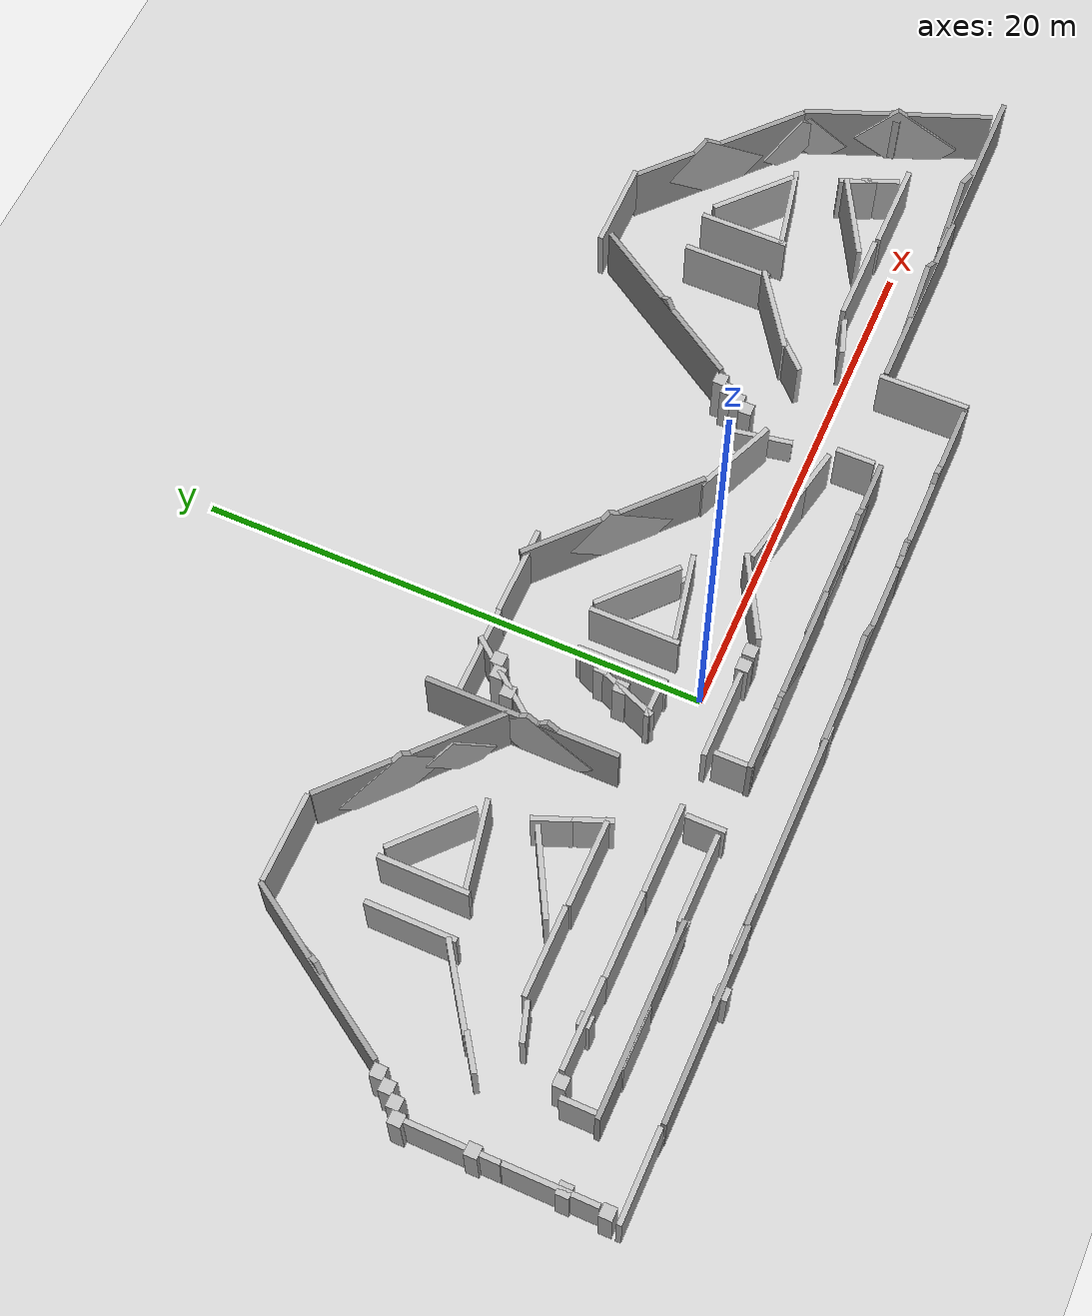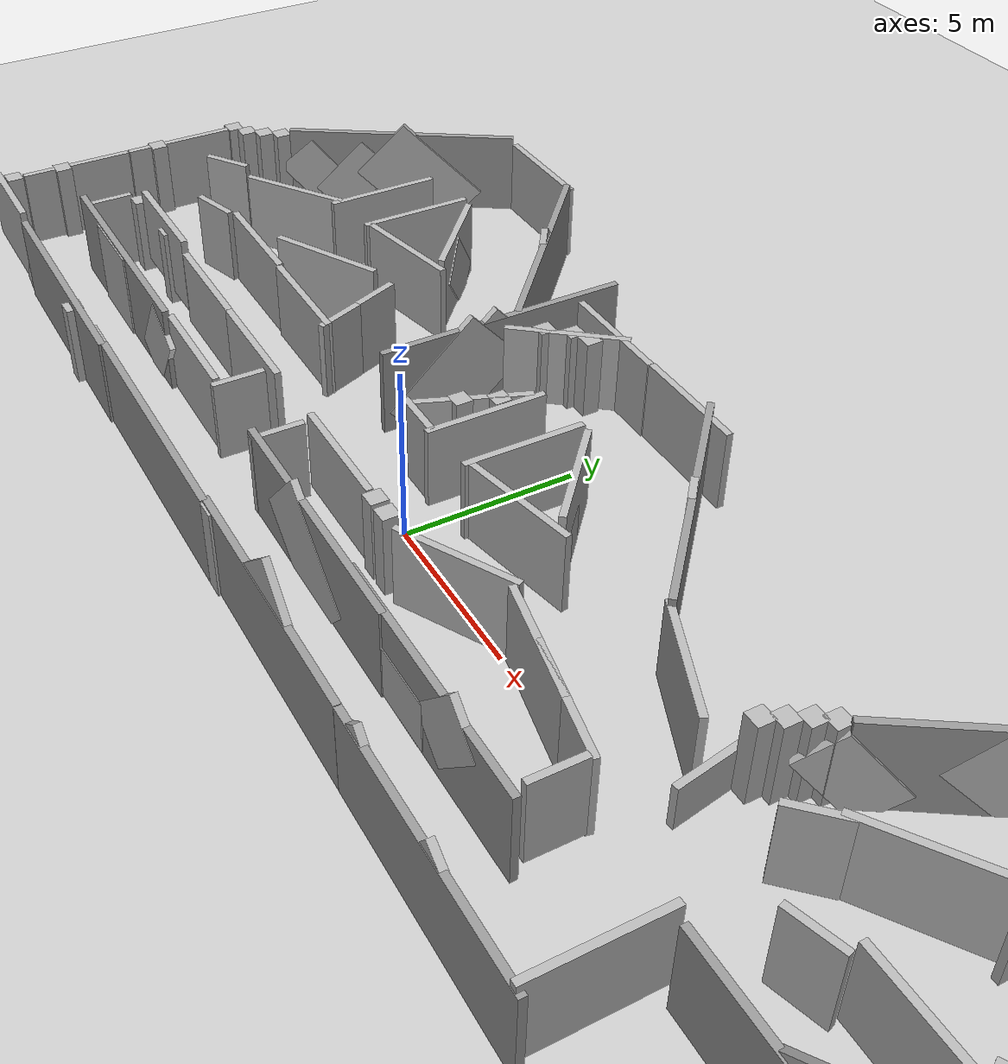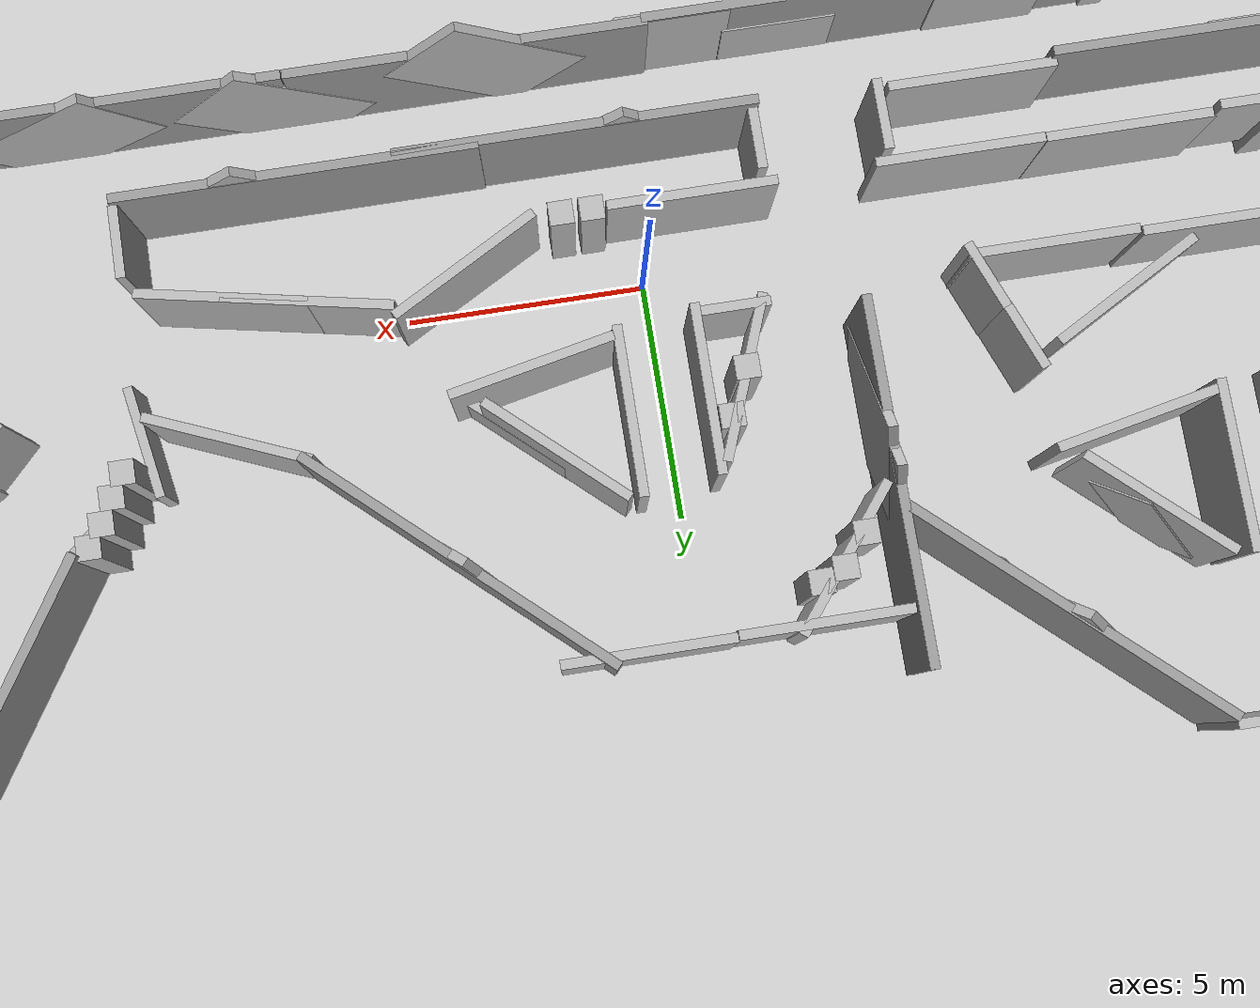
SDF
<sdf version="1.6">
 <world name="default">
  <light name="sun" type="directional">
   <pose>0 0 10 0 -0 0</pose>
   <diffuse>0.8 0.8 0.8 1</diffuse>
   <specular>0.1 0.1 0.1 1</specular>
   <attenuation>
    <range>1000</range>
    <constant>0.9</constant>
    <linear>0.01</linear>
    <quadratic>0.001</quadratic>
   </attenuation>
   <direction>-0.5 0.5 -1</direction>
  </light>
  <model name="ground_plane">
   <static>1</static>
   <link name="link">
    <collision name="collision">
     <geometry><plane><normal>0 0 1</normal><size>100 100</size></plane></geometry>
     <surface><friction><ode><mu>100</mu><mu2>50</mu2></ode></friction></surface>
    </collision>
    <visual name="visual">
     <cast_shadows>0</cast_shadows>
     <geometry><plane><normal>0 0 1</normal><size>100 100</size></plane></geometry>
     <material>
      <script><uri>file://media/materials/scripts/gazebo.material</uri><name>Gazebo/Grey</name></script>
     </material>
    </visual>
   </link>
  </model>
  <gravity>0 0 -9.8</gravity>
  <magnetic_field>6e-06 2.3e-05 -4.2e-05</magnetic_field>
  <atmosphere type="adiabatic"/>
  <physics name="default_physics" default="0" type="ode">
   <max_step_size>0.001</max_step_size>
   <real_time_factor>1</real_time_factor>
   <real_time_update_rate>0</real_time_update_rate>
  </physics>
  <scene><ambient>0.4 0.4 0.4 1</ambient><background>0.7 0.7 0.7 1</background><shadows>1</shadows></scene>
  <spherical_coordinates>
   <surface_model>EARTH_WGS84</surface_model>
   <latitude_deg>0</latitude_deg>
   <longitude_deg>0</longitude_deg>
   <elevation>0</elevation>
   <heading_deg>0</heading_deg>
  </spherical_coordinates>
  <model name="mywall_net10">
   <static>1</static>
   <link name="link">
    <pose>0 0 1.2 0 -0 0</pose>
    <collision name="collision"><geometry><box><size>1.5 0.2 2.4</size></box></geometry></collision>
    <visual name="visual">
     <cast_shadows>0</cast_shadows>
     <geometry><box><size>1.5 0.2 2.4</size></box></geometry>
     <material>
      <script>
       <uri>model://mywall_net10/materials/scripts</uri>
       <uri>model://mywall_net10/materials/textures</uri>
       <name>vrc/mywall_net10</name>
      </script>
     </material>
    </visual>
   </link>
   <pose>-1.56929 1.23265 0 0 -0 0</pose>
  </model>
  <model name="mywall_net3_clone">
   <static>1</static>
   <link name="link">
    <pose>0 0 1.2 0 -0 0</pose>
    <collision name="collision"><geometry><box><size>3.5 0.2 2.4</size></box></geometry></collision>
    <visual name="visual">
     <cast_shadows>0</cast_shadows>
     <geometry><box><size>3.5 0.2 2.4</size></box></geometry>
     <material>
      <script>
       <uri>model://mywall_net3/materials/scripts</uri>
       <uri>model://mywall_net3/materials/textures</uri>
       <name>vrc/mywall_net3</name>
      </script>
     </material>
    </visual>
   </link>
   <pose>-0.8 2.8 0 0 -0 1.57</pose>
  </model>
  <model name="mywall_net3_clone_0">
   <static>1</static>
   <link name="link">
    <pose>0 0 1.2 0 -0 0</pose>
    <collision name="collision"><geometry><box><size>3.5 0.2 2.4</size></box></geometry></collision>
    <visual name="visual">
     <cast_shadows>0</cast_shadows>
     <geometry><box><size>3.5 0.2 2.4</size></box></geometry>
     <material>
      <script>
       <uri>model://mywall_net3/materials/scripts</uri>
       <uri>model://mywall_net3/materials/textures</uri>
       <name>vrc/mywall_net3</name>
      </script>
     </material>
    </visual>
   </link>
   <pose>0.8 3 0 0 -0 1.57</pose>
  </model>
  <model name="mywall_net1">
   <static>1</static>
   <link name="link">
    <pose>0 0 1.2 0 -0 0</pose>
    <collision name="collision"><geometry><box><size>1.5 0.2 2.4</size></box></geometry></collision>
    <visual name="visual">
     <cast_shadows>0</cast_shadows>
     <geometry><box><size>1.5 0.2 2.4</size></box></geometry>
     <material>
      <script>
       <uri>model://mywall_net1/materials/scripts</uri>
       <uri>model://mywall_net1/materials/textures</uri>
       <name>vrc/mywall_net1</name>
      </script>
     </material>
    </visual>
   </link>
   <pose>-6.68814 1.38332 0 0 0 -1.2</pose>
  </model>
  <model name="mywall_net1_clone">
   <static>1</static>
   <link name="link">
    <pose>0 0 1.2 0 -0 0</pose>
    <collision name="collision"><geometry><box><size>1.5 0.2 2.4</size></box></geometry></collision>
    <visual name="visual">
     <cast_shadows>0</cast_shadows>
     <geometry><box><size>1.5 0.2 2.4</size></box></geometry>
     <material>
      <script>
       <uri>model://mywall_net1/materials/scripts</uri>
       <uri>model://mywall_net1/materials/textures</uri>
       <name>vrc/mywall_net1</name>
      </script>
     </material>
    </visual>
   </link>
   <pose>-7.22111 2.72216 0 0 0 -1.2</pose>
  </model>
  <model name="grey_wall_clone_clone_clone">
   <static>1</static>
   <link name="link">
    <pose>0 0 1.2 0 -0 0</pose>
    <collision name="collision"><geometry><box><size>7.5 0.2 2.8</size></box></geometry></collision>
    <visual name="visual">
     <cast_shadows>0</cast_shadows>
     <geometry><box><size>7.5 0.2 2.8</size></box></geometry>
     <material>
      <script>
       <uri>model://grey_wall/materials/scripts</uri>
       <uri>model://grey_wall/materials/textures</uri>
       <name>vrc/grey_wall</name>
      </script>
     </material>
    </visual>
   </link>
   <pose>-7.01787 8.23796 0 0 0 -0.735</pose>
  </model>
  <model name="mywall_net9">
   <static>1</static>
   <link name="link">
    <pose>0 0 1.2 0 -0 0</pose>
    <collision name="collision"><geometry><box><size>3.5 0.2 2.4</size></box></geometry></collision>
    <visual name="visual">
     <cast_shadows>0</cast_shadows>
     <geometry><box><size>3.5 0.2 2.4</size></box></geometry>
     <material>
      <script>
       <uri>model://mywall_net9/materials/scripts</uri>
       <uri>model://mywall_net9/materials/textures</uri>
       <name>vrc/mywall_net9</name>
      </script>
     </material>
    </visual>
   </link>
   <pose>2.6 1.8 0 0 -0 0.199999</pose>
  </model>
  <model name="mywall_net4_1_clone_0">
   <static>1</static>
   <link name="link">
    <pose>0 0 1.2 0 -0 0</pose>
    <collision name="collision"><geometry><box><size>3.5 0.2 2.4</size></box></geometry></collision>
    <visual name="visual">
     <cast_shadows>0</cast_shadows>
     <geometry><box><size>3.5 0.2 2.4</size></box></geometry>
     <material>
      <script>
       <uri>model://mywall_net4/materials/scripts</uri>
       <uri>model://mywall_net4/materials/textures</uri>
       <name>vrc/mywall_net4</name>
      </script>
     </material>
    </visual>
   </link>
   <pose>-10.8563 5.92454 0 0 -0 1.57</pose>
  </model>
  <model name="mywall_net2_1">
   <static>1</static>
   <link name="link">
    <pose>0 0 1.2 0 -0 0</pose>
    <collision name="collision"><geometry><box><size>3.5 0.2 2.4</size></box></geometry></collision>
    <visual name="visual">
     <cast_shadows>0</cast_shadows>
     <geometry><box><size>3.5 0.2 2.4</size></box></geometry>
     <material>
      <script>
       <uri>model://mywall_net2/materials/scripts</uri>
       <uri>model://mywall_net2/materials/textures</uri>
       <name>vrc/mywall_net2</name>
      </script>
     </material>
    </visual>
   </link>
   <pose>-9.12694 4.7 0 0 -0 0.199999</pose>
  </model>
  <model name="mywall_net5">
   <static>1</static>
   <link name="link">
    <pose>0 0 1.2 0 -0 0</pose>
    <collision name="collision"><geometry><box><size>3.5 0.2 2.4</size></box></geometry></collision>
    <visual name="visual">
     <cast_shadows>0</cast_shadows>
     <geometry><box><size>3.5 0.2 2.4</size></box></geometry>
     <material>
      <script>
       <uri>model://mywall_net5/materials/scripts</uri>
       <uri>model://mywall_net5/materials/textures</uri>
       <name>vrc/mywall_net5</name>
      </script>
     </material>
    </visual>
   </link>
   <pose>-8.15323 0.912168 0 0 -0 0</pose>
  </model>
  <model name="mywall_net5_clone">
   <static>1</static>
   <link name="link">
    <pose>0 0 1.2 0 -0 0</pose>
    <collision name="collision"><geometry><box><size>3.5 0.2 2.4</size></box></geometry></collision>
    <visual name="visual">
     <cast_shadows>0</cast_shadows>
     <geometry><box><size>3.5 0.2 2.4</size></box></geometry>
     <material>
      <script>
       <uri>model://mywall_net5/materials/scripts</uri>
       <uri>model://mywall_net5/materials/textures</uri>
       <name>vrc/mywall_net5</name>
      </script>
     </material>
    </visual>
   </link>
   <pose>-6.6459 -1.25646 0 0 -0 0</pose>
  </model>
  <model name="mywall_net10_0_clone">
   <static>1</static>
   <link name="link">
    <pose>0 0 1.2 0 -0 0</pose>
    <collision name="collision"><geometry><box><size>1.5 0.2 2.4</size></box></geometry></collision>
    <visual name="visual">
     <cast_shadows>0</cast_shadows>
     <geometry><box><size>1.5 0.2 2.4</size></box></geometry>
     <material>
      <script>
       <uri>model://mywall_net10/materials/scripts</uri>
       <uri>model://mywall_net10/materials/textures</uri>
       <name>vrc/mywall_net10</name>
      </script>
     </material>
    </visual>
   </link>
   <pose>-5.22714 -2.25073 0 0 -0 1.57</pose>
  </model>
  <model name="mywall_net8">
   <static>1</static>
   <link name="link">
    <pose>0 0 1.2 0 -0 0</pose>
    <collision name="collision"><geometry><box><size>3.5 0.2 2.4</size></box></geometry></collision>
    <visual name="visual">
     <cast_shadows>0</cast_shadows>
     <geometry><box><size>3.5 0.2 2.4</size></box></geometry>
     <material>
      <script>
       <uri>model://mywall_net8/materials/scripts</uri>
       <uri>model://mywall_net8/materials/textures</uri>
       <name>vrc/mywall_net8</name>
      </script>
     </material>
    </visual>
   </link>
   <pose>-1.13585 -1.2099 0 0 -0 0</pose>
  </model>
  <model name="mywall_net6_1">
   <static>1</static>
   <link name="link">
    <pose>0 0 1.2 0 -0 0</pose>
    <collision name="collision"><geometry><box><size>3.5 0.2 2.4</size></box></geometry></collision>
    <visual name="visual">
     <cast_shadows>0</cast_shadows>
     <geometry><box><size>3.5 0.2 2.4</size></box></geometry>
     <material>
      <script>
       <uri>model://mywall_net6/materials/scripts</uri>
       <uri>model://mywall_net6/materials/textures</uri>
       <name>vrc/mywall_net6</name>
      </script>
     </material>
    </visual>
   </link>
   <pose>-11.694 0.974828 0 0 -0 0</pose>
  </model>
  <model name="mywall_net6_1_clone">
   <static>1</static>
   <link name="link">
    <pose>0 0 1.2 0 -0 0</pose>
    <collision name="collision"><geometry><box><size>3.5 0.2 2.4</size></box></geometry></collision>
    <visual name="visual">
     <cast_shadows>0</cast_shadows>
     <geometry><box><size>3.5 0.2 2.4</size></box></geometry>
     <material>
      <script>
       <uri>model://mywall_net6/materials/scripts</uri>
       <uri>model://mywall_net6/materials/textures</uri>
       <name>vrc/mywall_net6</name>
      </script>
     </material>
    </visual>
   </link>
   <pose>-10.1548 -1.24656 0 0 -0 0</pose>
  </model>
  <model name="mywall_net6_1_clone_clone">
   <static>1</static>
   <link name="link">
    <pose>0 0 1.2 0 -0 0</pose>
    <collision name="collision"><geometry><box><size>3.5 0.2 2.4</size></box></geometry></collision>
    <visual name="visual">
     <cast_shadows>0</cast_shadows>
     <geometry><box><size>3.5 0.2 2.4</size></box></geometry>
     <material>
      <script>
       <uri>model://mywall_net6/materials/scripts</uri>
       <uri>model://mywall_net6/materials/textures</uri>
       <name>vrc/mywall_net6</name>
      </script>
     </material>
    </visual>
   </link>
   <pose>-13.6083 -1.25223 2.8 3.14 -0 0</pose>
  </model>
  <model name="mywall_net8_clone_clone">
   <static>1</static>
   <link name="link">
    <pose>0 0 1.2 0 -0 0</pose>
    <collision name="collision"><geometry><box><size>3.5 0.2 2.4</size></box></geometry></collision>
    <visual name="visual">
     <cast_shadows>0</cast_shadows>
     <geometry><box><size>3.5 0.2 2.4</size></box></geometry>
     <material>
      <script>
       <uri>model://mywall_net8/materials/scripts</uri>
       <uri>model://mywall_net8/materials/textures</uri>
       <name>vrc/mywall_net8</name>
      </script>
     </material>
    </visual>
   </link>
   <pose>-14 3.2 0 0 -0 0.6</pose>
  </model>
  <model name="mywall0">
   <static>1</static>
   <link name="link">
    <pose>0 0 1.2 0 -0 0</pose>
    <collision name="collision"><geometry><box><size>3.5 0.2 2.4</size></box></geometry></collision>
    <visual name="visual">
     <cast_shadows>0</cast_shadows>
     <geometry><box><size>3.5 0.2 2.4</size></box></geometry>
     <material>
      <script>
       <uri>model://mywall0/materials/scripts</uri>
       <uri>model://mywall0/materials/textures</uri>
       <name>vrc/mywall0</name>
      </script>
     </material>
    </visual>
   </link>
   <pose>-11.5252 10.8828 0 0 -0 0</pose>
  </model>
  <model name="mypillar_0">
   <static>1</static>
   <link name="link">
    <pose>0 0 1.2 0 -0 0</pose>
    <collision name="collision"><geometry><box><size>0.5 0.5 2.4</size></box></geometry></collision>
    <visual name="visual">
     <cast_shadows>0</cast_shadows>
     <geometry><box><size>0.5 0.5 2.4</size></box></geometry>
     <material>
      <script>
       <uri>model://mypillar/materials/scripts</uri>
       <uri>model://mypillar/materials/textures</uri>
       <name>vrc/mypillar</name>
      </script>
     </material>
    </visual>
   </link>
   <pose>-15.594 -1.34066 0 0 -0 0</pose>
  </model>
  <model name="mywall_net11_0_clone">
   <static>1</static>
   <link name="link">
    <pose>0 0 1.2 0 -0 0</pose>
    <collision name="collision"><geometry><box><size>1.5 0.2 2.4</size></box></geometry></collision>
    <visual name="visual">
     <cast_shadows>0</cast_shadows>
     <geometry><box><size>1.5 0.2 2.4</size></box></geometry>
     <material>
      <script>
       <uri>model://mywall_net11/materials/scripts</uri>
       <uri>model://mywall_net11/materials/textures</uri>
       <name>vrc/mywall_net11</name>
      </script>
     </material>
    </visual>
   </link>
   <pose>-16.0991 -2.23935 0 0 -0 1.57</pose>
  </model>
  <model name="mywall_net8_clone_clone_clone">
   <static>1</static>
   <link name="link">
    <pose>0 0 1.2 0 -0 0</pose>
    <collision name="collision"><geometry><box><size>3.5 0.2 2.4</size></box></geometry></collision>
    <visual name="visual">
     <cast_shadows>0</cast_shadows>
     <geometry><box><size>3.5 0.2 2.4</size></box></geometry>
     <material>
      <script>
       <uri>model://mywall_net8/materials/scripts</uri>
       <uri>model://mywall_net8/materials/textures</uri>
       <name>vrc/mywall_net8</name>
      </script>
     </material>
    </visual>
   </link>
   <pose>-9.26945 2.1763 2.8 3.14 -0 0.5</pose>
  </model>
  <model name="mywall_net11_1">
   <static>1</static>
   <link name="link">
    <pose>0 0 1.2 0 -0 0</pose>
    <collision name="collision"><geometry><box><size>1.5 0.2 2.4</size></box></geometry></collision>
    <visual name="visual">
     <cast_shadows>0</cast_shadows>
     <geometry><box><size>1.5 0.2 2.4</size></box></geometry>
     <material>
      <script>
       <uri>model://mywall_net11/materials/scripts</uri>
       <uri>model://mywall_net11/materials/textures</uri>
       <name>vrc/mywall_net11</name>
      </script>
     </material>
    </visual>
   </link>
   <pose>-14.2129 0.6 0 0 -0 0.3</pose>
  </model>
  <model name="grey_wall_0_clone">
   <static>1</static>
   <link name="link">
    <pose>0 0 1.2 0 -0 0</pose>
    <collision name="collision"><geometry><box><size>7.5 0.2 2.8</size></box></geometry></collision>
    <visual name="visual">
     <cast_shadows>0</cast_shadows>
     <geometry><box><size>7.5 0.2 2.8</size></box></geometry>
     <material>
      <script>
       <uri>model://grey_wall/materials/scripts</uri>
       <uri>model://grey_wall/materials/textures</uri>
       <name>vrc/grey_wall</name>
      </script>
     </material>
    </visual>
   </link>
   <pose>-15.4191 7.71104 0 0 -0 1</pose>
  </model>
  <model name="mywall_net4_1_clone_0_clone">
   <static>1</static>
   <link name="link">
    <pose>0 0 1.2 0 -0 0</pose>
    <collision name="collision"><geometry><box><size>3.5 0.2 2.4</size></box></geometry></collision>
    <visual name="visual">
     <cast_shadows>0</cast_shadows>
     <geometry><box><size>3.5 0.2 2.4</size></box></geometry>
     <material>
      <script>
       <uri>model://mywall_net4/materials/scripts</uri>
       <uri>model://mywall_net4/materials/textures</uri>
       <name>vrc/mywall_net4</name>
      </script>
     </material>
    </visual>
   </link>
   <pose>-12.5395 5.60797 0 0 -0 1.57</pose>
  </model>
  <model name="mywall_net7_1_clone">
   <static>1</static>
   <link name="link">
    <pose>0 0 1.2 0 -0 0</pose>
    <collision name="collision"><geometry><box><size>3.5 0.2 2.4</size></box></geometry></collision>
    <visual name="visual">
     <cast_shadows>0</cast_shadows>
     <geometry><box><size>3.5 0.2 2.4</size></box></geometry>
     <material>
      <script>
       <uri>model://mywall_net7/materials/scripts</uri>
       <uri>model://mywall_net7/materials/textures</uri>
       <name>vrc/mywall_net7</name>
      </script>
     </material>
    </visual>
   </link>
   <pose>-18.8571 1.13441 0 0 -0 1.57</pose>
  </model>
  <model name="mypillar_2">
   <static>1</static>
   <link name="link">
    <pose>0 0 1.2 0 -0 0</pose>
    <collision name="collision"><geometry><box><size>0.5 0.5 2.4</size></box></geometry></collision>
    <visual name="visual">
     <cast_shadows>0</cast_shadows>
     <geometry><box><size>0.5 0.5 2.4</size></box></geometry>
     <material>
      <script>
       <uri>model://mypillar/materials/scripts</uri>
       <uri>model://mypillar/materials/textures</uri>
       <name>vrc/mypillar</name>
      </script>
     </material>
    </visual>
   </link>
   <pose>-18.9055 3.11089 0 0 -0 0</pose>
  </model>
  <model name="mypillar_3">
   <static>1</static>
   <link name="link">
    <pose>0 0 1.2 0 -0 0</pose>
    <collision name="collision"><geometry><box><size>0.5 0.5 2.4</size></box></geometry></collision>
    <visual name="visual">
     <cast_shadows>0</cast_shadows>
     <geometry><box><size>0.5 0.5 2.4</size></box></geometry>
     <material>
      <script>
       <uri>model://mypillar/materials/scripts</uri>
       <uri>model://mypillar/materials/textures</uri>
       <name>vrc/mypillar</name>
      </script>
     </material>
    </visual>
   </link>
   <pose>-17.7063 4.33266 0 0 -0 0</pose>
  </model>
  <model name="mypillar_4">
   <static>1</static>
   <link name="link">
    <pose>0 0 1.2 0 -0 0</pose>
    <collision name="collision"><geometry><box><size>0.5 0.5 2.4</size></box></geometry></collision>
    <visual name="visual">
     <cast_shadows>0</cast_shadows>
     <geometry><box><size>0.5 0.5 2.4</size></box></geometry>
     <material>
      <script>
       <uri>model://mypillar/materials/scripts</uri>
       <uri>model://mypillar/materials/textures</uri>
       <name>vrc/mypillar</name>
      </script>
     </material>
    </visual>
   </link>
   <pose>-18.0478 3.84526 0 0 -0 0</pose>
  </model>
  <model name="mypillar_5">
   <static>1</static>
   <link name="link">
    <pose>0 0 1.2 0 -0 0</pose>
    <collision name="collision"><geometry><box><size>0.5 0.5 2.4</size></box></geometry></collision>
    <visual name="visual">
     <cast_shadows>0</cast_shadows>
     <geometry><box><size>0.5 0.5 2.4</size></box></geometry>
     <material>
      <script>
       <uri>model://mypillar/materials/scripts</uri>
       <uri>model://mypillar/materials/textures</uri>
       <name>vrc/mypillar</name>
      </script>
     </material>
    </visual>
   </link>
   <pose>-18.4243 3.39207 0 0 -0 0</pose>
  </model>
  <model name="mywall_net7_1_clone_clone">
   <static>1</static>
   <link name="link">
    <pose>0 0 1.2 0 -0 0</pose>
    <collision name="collision"><geometry><box><size>3.5 0.2 2.4</size></box></geometry></collision>
    <visual name="visual">
     <cast_shadows>0</cast_shadows>
     <geometry><box><size>3.5 0.2 2.4</size></box></geometry>
     <material>
      <script>
       <uri>model://mywall_net7/materials/scripts</uri>
       <uri>model://mywall_net7/materials/textures</uri>
       <name>vrc/mywall_net7</name>
      </script>
     </material>
    </visual>
   </link>
   <pose>-18.853 -2.40159 0 0 -0 1.57</pose>
  </model>
  <model name="mywall1">
   <static>1</static>
   <link name="link">
    <pose>0 0 1.2 0 -0 0</pose>
    <collision name="collision"><geometry><box><size>3.5 0.2 2.4</size></box></geometry></collision>
    <visual name="visual">
     <cast_shadows>0</cast_shadows>
     <geometry><box><size>3.5 0.2 2.4</size></box></geometry>
     <material>
      <script>
       <uri>model://mywall1/materials/scripts</uri>
       <uri>model://mywall1/materials/textures</uri>
       <name>vrc/mywall1</name>
      </script>
     </material>
    </visual>
   </link>
   <pose>-2.324 7.71624 0 0 -0 0</pose>
  </model>
  <model name="mywall1_0">
   <static>1</static>
   <link name="link">
    <pose>0 0 1.2 0 -0 0</pose>
    <collision name="collision"><geometry><box><size>3.5 0.2 2.4</size></box></geometry></collision>
    <visual name="visual">
     <cast_shadows>0</cast_shadows>
     <geometry><box><size>3.5 0.2 2.4</size></box></geometry>
     <material>
      <script>
       <uri>model://mywall1/materials/scripts</uri>
       <uri>model://mywall1/materials/textures</uri>
       <name>vrc/mywall1</name>
      </script>
     </material>
    </visual>
   </link>
   <pose>1.18748 7.74669 0 0 -0 0</pose>
  </model>
  <model name="grey_wall_clone_clone_clone_clone">
   <static>1</static>
   <link name="link">
    <pose>0 0 1.2 0 -0 0</pose>
    <collision name="collision"><geometry><box><size>7.5 0.2 2.8</size></box></geometry></collision>
    <visual name="visual">
     <cast_shadows>0</cast_shadows>
     <geometry><box><size>7.5 0.2 2.8</size></box></geometry>
     <material>
      <script>
       <uri>model://grey_wall/materials/scripts</uri>
       <uri>model://grey_wall/materials/textures</uri>
       <name>vrc/grey_wall</name>
      </script>
     </material>
    </visual>
   </link>
   <pose>4.57876 5.44143 0 0 0 -0.735</pose>
  </model>
  <model name="mywall_net8_clone_clone_0">
   <static>1</static>
   <link name="link">
    <pose>0 0 1.2 0 -0 0</pose>
    <collision name="collision"><geometry><box><size>3.5 0.2 2.4</size></box></geometry></collision>
    <visual name="visual">
     <cast_shadows>0</cast_shadows>
     <geometry><box><size>3.5 0.2 2.4</size></box></geometry>
     <material>
      <script>
       <uri>model://mywall_net8/materials/scripts</uri>
       <uri>model://mywall_net8/materials/textures</uri>
       <name>vrc/mywall_net8</name>
      </script>
     </material>
    </visual>
   </link>
   <pose>3.62528 -0.456702 0 0 -0 0.5</pose>
  </model>
  <model name="mypillar_1_clone">
   <static>1</static>
   <link name="link">
    <pose>0 0 1.2 0 -0 0</pose>
    <collision name="collision"><geometry><box><size>0.5 0.5 2.4</size></box></geometry></collision>
    <visual name="visual">
     <cast_shadows>0</cast_shadows>
     <geometry><box><size>0.5 0.5 2.4</size></box></geometry>
     <material>
      <script>
       <uri>model://mypillar/materials/scripts</uri>
       <uri>model://mypillar/materials/textures</uri>
       <name>vrc/mypillar</name>
      </script>
     </material>
    </visual>
   </link>
   <pose>0.920022 -1.2 0 0 -0 0</pose>
  </model>
  <model name="mypillar_1_clone_0">
   <static>1</static>
   <link name="link">
    <pose>0 0 1.2 0 -0 0</pose>
    <collision name="collision"><geometry><box><size>0.5 0.5 2.4</size></box></geometry></collision>
    <visual name="visual">
     <cast_shadows>0</cast_shadows>
     <geometry><box><size>0.5 0.5 2.4</size></box></geometry>
     <material>
      <script>
       <uri>model://mypillar/materials/scripts</uri>
       <uri>model://mypillar/materials/textures</uri>
       <name>vrc/mypillar</name>
      </script>
     </material>
    </visual>
   </link>
   <pose>1.54699 -1.2 0 0 -0 0</pose>
  </model>
  <model name="mywall_net5_0">
   <static>1</static>
   <link name="link">
    <pose>0 0 1.2 0 -0 0</pose>
    <collision name="collision"><geometry><box><size>3.5 0.2 2.4</size></box></geometry></collision>
    <visual name="visual">
     <cast_shadows>0</cast_shadows>
     <geometry><box><size>3.5 0.2 2.4</size></box></geometry>
     <material>
      <script>
       <uri>model://mywall_net5/materials/scripts</uri>
       <uri>model://mywall_net5/materials/textures</uri>
       <name>vrc/mywall_net5</name>
      </script>
     </material>
    </visual>
   </link>
   <pose>20.1 4.60268 0 0 -0 0.2</pose>
  </model>
  <model name="mywall_net9_0_clone">
   <static>1</static>
   <link name="link">
    <pose>0 0 1.2 0 -0 0</pose>
    <collision name="collision"><geometry><box><size>3.5 0.2 2.4</size></box></geometry></collision>
    <visual name="visual">
     <cast_shadows>0</cast_shadows>
     <geometry><box><size>3.5 0.2 2.4</size></box></geometry>
     <material>
      <script>
       <uri>model://mywall_net9/materials/scripts</uri>
       <uri>model://mywall_net9/materials/textures</uri>
       <name>vrc/mywall_net9</name>
      </script>
     </material>
    </visual>
   </link>
   <pose>18.4091 5.82039 0 0 -0 1.57</pose>
  </model>
  <model name="mywall_net9_0_clone_0">
   <static>1</static>
   <link name="link">
    <pose>0 0 1.2 0 -0 0</pose>
    <collision name="collision"><geometry><box><size>3.5 0.2 2.4</size></box></geometry></collision>
    <visual name="visual">
     <cast_shadows>0</cast_shadows>
     <geometry><box><size>3.5 0.2 2.4</size></box></geometry>
     <material>
      <script>
       <uri>model://mywall_net9/materials/scripts</uri>
       <uri>model://mywall_net9/materials/textures</uri>
       <name>vrc/mywall_net9</name>
      </script>
     </material>
    </visual>
   </link>
   <pose>16.7773 5.8484 0 0 -0 1.57</pose>
  </model>
  <model name="mywall_net3_clone_clone_clone">
   <static>1</static>
   <link name="link">
    <pose>0 0 1.2 0 -0 0</pose>
    <collision name="collision"><geometry><box><size>3.5 0.2 2.4</size></box></geometry></collision>
    <visual name="visual">
     <cast_shadows>0</cast_shadows>
     <geometry><box><size>3.5 0.2 2.4</size></box></geometry>
     <material>
      <script>
       <uri>model://mywall_net3/materials/scripts</uri>
       <uri>model://mywall_net3/materials/textures</uri>
       <name>vrc/mywall_net3</name>
      </script>
     </material>
    </visual>
   </link>
   <pose>15.2159 3.31968 2.8 3.14 1e-06 0.6</pose>
  </model>
  <model name="grey_wall_0_clone_clone">
   <static>1</static>
   <link name="link">
    <pose>0 0 1.2 0 -0 0</pose>
    <collision name="collision"><geometry><box><size>7.5 0.2 2.8</size></box></geometry></collision>
    <visual name="visual">
     <cast_shadows>0</cast_shadows>
     <geometry><box><size>7.5 0.2 2.8</size></box></geometry>
     <material>
      <script>
       <uri>model://grey_wall/materials/scripts</uri>
       <uri>model://grey_wall/materials/textures</uri>
       <name>vrc/grey_wall</name>
      </script>
     </material>
    </visual>
   </link>
   <pose>13.9841 7.31333 0 0 -0 1</pose>
  </model>
  <model name="mywall_net8_clone">
   <static>1</static>
   <link name="link">
    <pose>0 0 1.2 0 -0 0</pose>
    <collision name="collision"><geometry><box><size>3.5 0.2 2.4</size></box></geometry></collision>
    <visual name="visual">
     <cast_shadows>0</cast_shadows>
     <geometry><box><size>3.5 0.2 2.4</size></box></geometry>
     <material>
      <script>
       <uri>model://mywall_net8/materials/scripts</uri>
       <uri>model://mywall_net8/materials/textures</uri>
       <name>vrc/mywall_net8</name>
      </script>
     </material>
    </visual>
   </link>
   <pose>17.2655 10.6912 2.8 -3.14018 0 0</pose>
  </model>
  <model name="grey_wall_clone_clone_clone_clone_0">
   <static>1</static>
   <link name="link">
    <pose>0 0 1.2 0 -0 0</pose>
    <collision name="collision"><geometry><box><size>7.5 0.2 2.8</size></box></geometry></collision>
    <visual name="visual">
     <cast_shadows>0</cast_shadows>
     <geometry><box><size>7.5 0.2 2.8</size></box></geometry>
     <material>
      <script>
       <uri>model://grey_wall/materials/scripts</uri>
       <uri>model://grey_wall/materials/textures</uri>
       <name>vrc/grey_wall</name>
      </script>
     </material>
    </visual>
   </link>
   <pose>21.7169 8.20586 0 0 0 -0.735</pose>
  </model>
  <model name="mywall_net8_clone_clone_clone_clone">
   <static>1</static>
   <link name="link">
    <pose>0 0 1.2 0 -0 0</pose>
    <collision name="collision"><geometry><box><size>3.5 0.2 2.4</size></box></geometry></collision>
    <visual name="visual">
     <cast_shadows>0</cast_shadows>
     <geometry><box><size>3.5 0.2 2.4</size></box></geometry>
     <material>
      <script>
       <uri>model://mywall_net8/materials/scripts</uri>
       <uri>model://mywall_net8/materials/textures</uri>
       <name>vrc/mywall_net8</name>
      </script>
     </material>
    </visual>
   </link>
   <pose>20.4573 2.1 2.8 3.14 -0 0.5</pose>
  </model>
  <model name="mywall_net0_2_clone">
   <static>1</static>
   <link name="link">
    <pose>0 0 1.2 0 -0 0</pose>
    <collision name="collision"><geometry><box><size>1.5 0.2 2.4</size></box></geometry></collision>
    <visual name="visual">
     <cast_shadows>0</cast_shadows>
     <geometry><box><size>1.5 0.2 2.4</size></box></geometry>
     <material>
      <script>
       <uri>model://mywall_net0/materials/scripts</uri>
       <uri>model://mywall_net0/materials/textures</uri>
       <name>vrc/mywall_net0</name>
      </script>
     </material>
    </visual>
   </link>
   <pose>22.357 2.55704 0 0 0 -1.2</pose>
  </model>
  <model name="mywall_net0_2_clone_0">
   <static>1</static>
   <link name="link">
    <pose>0 0 1.2 0 -0 0</pose>
    <collision name="collision"><geometry><box><size>1.5 0.2 2.4</size></box></geometry></collision>
    <visual name="visual">
     <cast_shadows>0</cast_shadows>
     <geometry><box><size>1.5 0.2 2.4</size></box></geometry>
     <material>
      <script>
       <uri>model://mywall_net0/materials/scripts</uri>
       <uri>model://mywall_net0/materials/textures</uri>
       <name>vrc/mywall_net0</name>
      </script>
     </material>
    </visual>
   </link>
   <pose>22.7032 1.75094 0 0 0 -1.2</pose>
  </model>
  <model name="grey_wall_clone_clone_clone_clone_0_clone_clone">
   <static>1</static>
   <link name="link">
    <pose>0 0 1.2 0 -0 0</pose>
    <collision name="collision"><geometry><box><size>7.5 0.2 2.8</size></box></geometry></collision>
    <visual name="visual">
     <cast_shadows>0</cast_shadows>
     <geometry><box><size>7.5 0.2 2.8</size></box></geometry>
     <material>
      <script>
       <uri>model://grey_wall/materials/scripts</uri>
       <uri>model://grey_wall/materials/textures</uri>
       <name>vrc/grey_wall</name>
      </script>
     </material>
    </visual>
   </link>
   <pose>25.9236 2.21742 0 0 0 -1.2</pose>
  </model>
  <model name="mywall0_clone">
   <static>1</static>
   <link name="link">
    <pose>0 0 1.2 0 -0 0</pose>
    <collision name="collision"><geometry><box><size>3.5 0.2 2.4</size></box></geometry></collision>
    <visual name="visual">
     <cast_shadows>0</cast_shadows>
     <geometry><box><size>3.5 0.2 2.4</size></box></geometry>
     <material>
      <script>
       <uri>model://mywall0/materials/scripts</uri>
       <uri>model://mywall0/materials/textures</uri>
       <name>vrc/mywall0</name>
      </script>
     </material>
    </visual>
   </link>
   <pose>6.82844 -0.184627 0 0 0 -0.2</pose>
  </model>
  <model name="mywall0_clone_clone">
   <static>1</static>
   <link name="link">
    <pose>0 0 1.2 0 -0 0</pose>
    <collision name="collision"><geometry><box><size>3.5 0.2 2.4</size></box></geometry></collision>
    <visual name="visual">
     <cast_shadows>0</cast_shadows>
     <geometry><box><size>3.5 0.2 2.4</size></box></geometry>
     <material>
      <script>
       <uri>model://mywall0/materials/scripts</uri>
       <uri>model://mywall0/materials/textures</uri>
       <name>vrc/mywall0</name>
      </script>
     </material>
    </visual>
   </link>
   <pose>8.52847 -0.528615 0 0 0 -0.2</pose>
  </model>
  <model name="mywall_net4_1_clone_0_clone_clone_clone">
   <static>1</static>
   <link name="link">
    <pose>0 0 1.2 0 -0 0</pose>
    <collision name="collision"><geometry><box><size>3.5 0.2 2.4</size></box></geometry></collision>
    <visual name="visual">
     <cast_shadows>0</cast_shadows>
     <geometry><box><size>3.5 0.2 2.4</size></box></geometry>
     <material>
      <script>
       <uri>model://mywall_net4/materials/scripts</uri>
       <uri>model://mywall_net4/materials/textures</uri>
       <name>vrc/mywall_net4</name>
      </script>
     </material>
    </visual>
   </link>
   <pose>21.5223 0.789609 2.8 3.14 -0 0</pose>
  </model>
  <model name="mywall_net4_1_clone_0_clone_clone_clone_clone">
   <static>1</static>
   <link name="link">
    <pose>0 0 1.2 0 -0 0</pose>
    <collision name="collision"><geometry><box><size>3.5 0.2 2.4</size></box></geometry></collision>
    <visual name="visual">
     <cast_shadows>0</cast_shadows>
     <geometry><box><size>3.5 0.2 2.4</size></box></geometry>
     <material>
      <script>
       <uri>model://mywall_net4/materials/scripts</uri>
       <uri>model://mywall_net4/materials/textures</uri>
       <name>vrc/mywall_net4</name>
      </script>
     </material>
    </visual>
   </link>
   <pose>17.8818 0.850706 2.8 3.14 -0 0</pose>
  </model>
  <model name="mywall_net0_3">
   <static>1</static>
   <link name="link">
    <pose>0 0 1.2 0 -0 0</pose>
    <collision name="collision"><geometry><box><size>1.5 0.2 2.4</size></box></geometry></collision>
    <visual name="visual">
     <cast_shadows>0</cast_shadows>
     <geometry><box><size>1.5 0.2 2.4</size></box></geometry>
     <material>
      <script>
       <uri>model://mywall_net0/materials/scripts</uri>
       <uri>model://mywall_net0/materials/textures</uri>
       <name>vrc/mywall_net0</name>
      </script>
     </material>
    </visual>
   </link>
   <pose>15.3715 0.509738 0 0 -0 0.3</pose>
  </model>
  <model name="mywall_net2_1_clone">
   <static>1</static>
   <link name="link">
    <pose>0 0 1.2 0 -0 0</pose>
    <collision name="collision"><geometry><box><size>3.5 0.2 2.4</size></box></geometry></collision>
    <visual name="visual">
     <cast_shadows>0</cast_shadows>
     <geometry><box><size>3.5 0.2 2.4</size></box></geometry>
     <material>
      <script>
       <uri>model://mywall_net2/materials/scripts</uri>
       <uri>model://mywall_net2/materials/textures</uri>
       <name>vrc/mywall_net2</name>
      </script>
     </material>
    </visual>
   </link>
   <pose>8.7594 2.32284 0 0 0 -0.4</pose>
  </model>
  <model name="mypillar_1_clone_0_clone">
   <static>1</static>
   <link name="link">
    <pose>0 0 1.2 0 -0 0</pose>
    <collision name="collision"><geometry><box><size>0.5 0.5 2.4</size></box></geometry></collision>
    <visual name="visual">
     <cast_shadows>0</cast_shadows>
     <geometry><box><size>0.5 0.5 2.4</size></box></geometry>
     <material>
      <script>
       <uri>model://mypillar/materials/scripts</uri>
       <uri>model://mypillar/materials/textures</uri>
       <name>vrc/mypillar</name>
      </script>
     </material>
    </visual>
   </link>
   <pose>10.8687 2.68887 0 0 -0 0</pose>
  </model>
  <model name="mypillar_1_clone_0_clone_0">
   <static>1</static>
   <link name="link">
    <pose>0 0 1.2 0 -0 0</pose>
    <collision name="collision"><geometry><box><size>0.5 0.5 2.4</size></box></geometry></collision>
    <visual name="visual">
     <cast_shadows>0</cast_shadows>
     <geometry><box><size>0.5 0.5 2.4</size></box></geometry>
     <material>
      <script>
       <uri>model://mypillar/materials/scripts</uri>
       <uri>model://mypillar/materials/textures</uri>
       <name>vrc/mypillar</name>
      </script>
     </material>
    </visual>
   </link>
   <pose>11.1303 3.14665 0 0 -0 0</pose>
  </model>
  <model name="mypillar_1_clone_0_clone_1">
   <static>1</static>
   <link name="link">
    <pose>0 0 1.2 0 -0 0</pose>
    <collision name="collision"><geometry><box><size>0.5 0.5 2.4</size></box></geometry></collision>
    <visual name="visual">
     <cast_shadows>0</cast_shadows>
     <geometry><box><size>0.5 0.5 2.4</size></box></geometry>
     <material>
      <script>
       <uri>model://mypillar/materials/scripts</uri>
       <uri>model://mypillar/materials/textures</uri>
       <name>vrc/mypillar</name>
      </script>
     </material>
    </visual>
   </link>
   <pose>11.3906 3.64228 0 0 -0 0</pose>
  </model>
  <model name="mypillar_1_clone_0_clone_2">
   <static>1</static>
   <link name="link">
    <pose>0 0 1.2 0 -0 0</pose>
    <collision name="collision"><geometry><box><size>0.5 0.5 2.4</size></box></geometry></collision>
    <visual name="visual">
     <cast_shadows>0</cast_shadows>
     <geometry><box><size>0.5 0.5 2.4</size></box></geometry>
     <material>
      <script>
       <uri>model://mypillar/materials/scripts</uri>
       <uri>model://mypillar/materials/textures</uri>
       <name>vrc/mypillar</name>
      </script>
     </material>
    </visual>
   </link>
   <pose>11.6902 4.0623 0 0 -0 0</pose>
  </model>
  <model name="mywall_net11_0_clone_clone">
   <static>1</static>
   <link name="link">
    <pose>0 0 1.2 0 -0 0</pose>
    <collision name="collision"><geometry><box><size>1.5 0.2 2.4</size></box></geometry></collision>
    <visual name="visual">
     <cast_shadows>0</cast_shadows>
     <geometry><box><size>1.5 0.2 2.4</size></box></geometry>
     <material>
      <script>
       <uri>model://mywall_net11/materials/scripts</uri>
       <uri>model://mywall_net11/materials/textures</uri>
       <name>vrc/mywall_net11</name>
      </script>
     </material>
    </visual>
   </link>
   <pose>10.3494 -1.85373 2.8 3.14 0 1.57</pose>
  </model>
  <model name="mywall_net2_1_clone_0_clone">
   <static>1</static>
   <link name="link">
    <pose>0 0 1.2 0 -0 0</pose>
    <collision name="collision"><geometry><box><size>3.5 0.2 2.4</size></box></geometry></collision>
    <visual name="visual">
     <cast_shadows>0</cast_shadows>
     <geometry><box><size>3.5 0.2 2.4</size></box></geometry>
     <material>
      <script>
       <uri>model://mywall_net2/materials/scripts</uri>
       <uri>model://mywall_net2/materials/textures</uri>
       <name>vrc/mywall_net2</name>
      </script>
     </material>
    </visual>
   </link>
   <pose>14 -3.20841 2.8 3.14 -1e-06 1.57</pose>
  </model>
  <model name="grey_wall_1">
   <static>1</static>
   <link name="link">
    <pose>0 0 1.2 0 -0 0</pose>
    <collision name="collision"><geometry><box><size>7.5 0.2 2.8</size></box></geometry></collision>
    <visual name="visual">
     <cast_shadows>0</cast_shadows>
     <geometry><box><size>7.5 0.2 2.8</size></box></geometry>
     <material>
      <script>
       <uri>model://grey_wall/materials/scripts</uri>
       <uri>model://grey_wall/materials/textures</uri>
       <name>vrc/grey_wall</name>
      </script>
     </material>
    </visual>
   </link>
   <pose>18.0374 -1.61457 0 0 -0 0</pose>
  </model>
  <model name="grey_wall_2">
   <static>1</static>
   <link name="link">
    <pose>0 0 1.2 0 -0 0</pose>
    <collision name="collision"><geometry><box><size>7.5 0.2 2.8</size></box></geometry></collision>
    <visual name="visual">
     <cast_shadows>0</cast_shadows>
     <geometry><box><size>7.5 0.2 2.8</size></box></geometry>
     <material>
      <script>
       <uri>model://grey_wall/materials/scripts</uri>
       <uri>model://grey_wall/materials/textures</uri>
       <name>vrc/grey_wall</name>
      </script>
     </material>
    </visual>
   </link>
   <pose>24.2897 -1.53015 0 0 -0 0</pose>
  </model>
  <model name="grey_wall_2_clone">
   <static>1</static>
   <link name="link">
    <pose>0 0 1.2 0 -0 0</pose>
    <collision name="collision"><geometry><box><size>7.5 0.2 2.8</size></box></geometry></collision>
    <visual name="visual">
     <cast_shadows>0</cast_shadows>
     <geometry><box><size>7.5 0.2 2.8</size></box></geometry>
     <material>
      <script>
       <uri>model://grey_wall/materials/scripts</uri>
       <uri>model://grey_wall/materials/textures</uri>
       <name>vrc/grey_wall</name>
      </script>
     </material>
    </visual>
   </link>
   <pose>6.72766 -2.82714 0 0 -0 0</pose>
  </model>
  <model name="grey_wall_2_clone_0">
   <static>1</static>
   <link name="link">
    <pose>0 0 1.2 0 -0 0</pose>
    <collision name="collision"><geometry><box><size>7.5 0.2 2.8</size></box></geometry></collision>
    <visual name="visual">
     <cast_shadows>0</cast_shadows>
     <geometry><box><size>7.5 0.2 2.8</size></box></geometry>
     <material>
      <script>
       <uri>model://grey_wall/materials/scripts</uri>
       <uri>model://grey_wall/materials/textures</uri>
       <name>vrc/grey_wall</name>
      </script>
     </material>
    </visual>
   </link>
   <pose>0.993119 -2.88058 0 0 -0 0</pose>
  </model>
  <model name="grey_wall_2_clone_1">
   <static>1</static>
   <link name="link">
    <pose>0 0 1.2 0 -0 0</pose>
    <collision name="collision"><geometry><box><size>7.5 0.2 2.8</size></box></geometry></collision>
    <visual name="visual">
     <cast_shadows>0</cast_shadows>
     <geometry><box><size>7.5 0.2 2.8</size></box></geometry>
     <material>
      <script>
       <uri>model://grey_wall/materials/scripts</uri>
       <uri>model://grey_wall/materials/textures</uri>
       <name>vrc/grey_wall</name>
      </script>
     </material>
    </visual>
   </link>
   <pose>10.4704 -4.87772 0 0 -0 0</pose>
  </model>
  <model name="grey_wall_2_clone_2">
   <static>1</static>
   <link name="link">
    <pose>0 0 1.2 0 -0 0</pose>
    <collision name="collision"><geometry><box><size>7.5 0.2 2.8</size></box></geometry></collision>
    <visual name="visual">
     <cast_shadows>0</cast_shadows>
     <geometry><box><size>7.5 0.2 2.8</size></box></geometry>
     <material>
      <script>
       <uri>model://grey_wall/materials/scripts</uri>
       <uri>model://grey_wall/materials/textures</uri>
       <name>vrc/grey_wall</name>
      </script>
     </material>
    </visual>
   </link>
   <pose>2.94832 -4.87324 0 0 -0 0</pose>
  </model>
  <model name="grey_wall_2_clone_3">
   <static>1</static>
   <link name="link">
    <pose>0 0 1.2 0 -0 0</pose>
    <collision name="collision"><geometry><box><size>7.5 0.2 2.8</size></box></geometry></collision>
    <visual name="visual">
     <cast_shadows>0</cast_shadows>
     <geometry><box><size>7.5 0.2 2.8</size></box></geometry>
     <material>
      <script>
       <uri>model://grey_wall/materials/scripts</uri>
       <uri>model://grey_wall/materials/textures</uri>
       <name>vrc/grey_wall</name>
      </script>
     </material>
    </visual>
   </link>
   <pose>-4.42445 -4.94188 0 0 -0 0</pose>
  </model>
  <model name="grey_wall_2_clone_4">
   <static>1</static>
   <link name="link">
    <pose>0 0 1.2 0 -0 0</pose>
    <collision name="collision"><geometry><box><size>7.5 0.2 2.8</size></box></geometry></collision>
    <visual name="visual">
     <cast_shadows>0</cast_shadows>
     <geometry><box><size>7.5 0.2 2.8</size></box></geometry>
     <material>
      <script>
       <uri>model://grey_wall/materials/scripts</uri>
       <uri>model://grey_wall/materials/textures</uri>
       <name>vrc/grey_wall</name>
      </script>
     </material>
    </visual>
   </link>
   <pose>-11.8717 -5.01121 0 0 -0 0</pose>
  </model>
  <model name="mywall_net7_1_clone_clone_clone_clone">
   <static>1</static>
   <link name="link">
    <pose>0 0 1.2 0 -0 0</pose>
    <collision name="collision"><geometry><box><size>3.5 0.2 2.4</size></box></geometry></collision>
    <visual name="visual">
     <cast_shadows>0</cast_shadows>
     <geometry><box><size>3.5 0.2 2.4</size></box></geometry>
     <material>
      <script>
       <uri>model://mywall_net7/materials/scripts</uri>
       <uri>model://mywall_net7/materials/textures</uri>
       <name>vrc/mywall_net7</name>
      </script>
     </material>
    </visual>
   </link>
   <pose>-17.5118 -4.9727 2.8 3.14 -0 0</pose>
  </model>
  <model name="mypillar_4_clone">
   <static>1</static>
   <link name="link">
    <pose>0 0 1.2 0 -0 0</pose>
    <collision name="collision"><geometry><box><size>0.5 0.5 2.4</size></box></geometry></collision>
    <visual name="visual">
     <cast_shadows>0</cast_shadows>
     <geometry><box><size>0.5 0.5 2.4</size></box></geometry>
     <material>
      <script>
       <uri>model://mypillar/materials/scripts</uri>
       <uri>model://mypillar/materials/textures</uri>
       <name>vrc/mypillar</name>
      </script>
     </material>
    </visual>
   </link>
   <pose>-18.9241 -4.45153 0 0 -0 0</pose>
  </model>
  <model name="grey_wall_2_clone_0_clone">
   <static>1</static>
   <link name="link">
    <pose>0 0 1.2 0 -0 0</pose>
    <collision name="collision"><geometry><box><size>7.5 0.2 2.8</size></box></geometry></collision>
    <visual name="visual">
     <cast_shadows>0</cast_shadows>
     <geometry><box><size>7.5 0.2 2.8</size></box></geometry>
     <material>
      <script>
       <uri>model://grey_wall/materials/scripts</uri>
       <uri>model://grey_wall/materials/textures</uri>
       <name>vrc/grey_wall</name>
      </script>
     </material>
    </visual>
   </link>
   <pose>-12.5864 -2.95024 0 0 -0 0</pose>
  </model>
  <model name="mywall_net6_1_clone_clone_0">
   <static>1</static>
   <link name="link">
    <pose>0 0 1.2 0 -0 0</pose>
    <collision name="collision"><geometry><box><size>3.5 0.2 2.4</size></box></geometry></collision>
    <visual name="visual">
     <cast_shadows>0</cast_shadows>
     <geometry><box><size>3.5 0.2 2.4</size></box></geometry>
     <material>
      <script>
       <uri>model://mywall_net6/materials/scripts</uri>
       <uri>model://mywall_net6/materials/textures</uri>
       <name>vrc/mywall_net6</name>
      </script>
     </material>
    </visual>
   </link>
   <pose>-7.18332 -2.79881 0 0 -0 0</pose>
  </model>
  <model name="mywall_net6_1_clone_clone_1">
   <static>1</static>
   <link name="link">
    <pose>0 0 1.2 0 -0 0</pose>
    <collision name="collision"><geometry><box><size>3.5 0.2 2.4</size></box></geometry></collision>
    <visual name="visual">
     <cast_shadows>0</cast_shadows>
     <geometry><box><size>3.5 0.2 2.4</size></box></geometry>
     <material>
      <script>
       <uri>model://mywall_net6/materials/scripts</uri>
       <uri>model://mywall_net6/materials/textures</uri>
       <name>vrc/mywall_net6</name>
      </script>
     </material>
    </visual>
   </link>
   <pose>-14.0457 -5.01069 0 0 1.57 0</pose>
  </model>
  <model name="mywall_net5_clone_clone">
   <static>1</static>
   <link name="link">
    <pose>0 0 1.2 0 -0 0</pose>
    <collision name="collision"><geometry><box><size>3.5 0.2 2.4</size></box></geometry></collision>
    <visual name="visual">
     <cast_shadows>0</cast_shadows>
     <geometry><box><size>3.5 0.2 2.4</size></box></geometry>
     <material>
      <script>
       <uri>model://mywall_net5/materials/scripts</uri>
       <uri>model://mywall_net5/materials/textures</uri>
       <name>vrc/mywall_net5</name>
      </script>
     </material>
    </visual>
   </link>
   <pose>-9.32003 -4.9 0.7 0 1.57 0</pose>
  </model>
  <model name="mywall_net3_clone_clone">
   <static>1</static>
   <link name="link">
    <pose>0 0 1.2 0 -0 0</pose>
    <collision name="collision"><geometry><box><size>3.5 0.2 2.4</size></box></geometry></collision>
    <visual name="visual">
     <cast_shadows>0</cast_shadows>
     <geometry><box><size>3.5 0.2 2.4</size></box></geometry>
     <material>
      <script>
       <uri>model://mywall_net3/materials/scripts</uri>
       <uri>model://mywall_net3/materials/textures</uri>
       <name>vrc/mywall_net3</name>
      </script>
     </material>
    </visual>
   </link>
   <pose>-2.51695 -4.94104 0.8 0 1.57 0</pose>
  </model>
  <model name="mywall_net10_0_clone_clone">
   <static>1</static>
   <link name="link">
    <pose>0 0 1.2 0 -0 0</pose>
    <collision name="collision"><geometry><box><size>1.5 0.2 2.4</size></box></geometry></collision>
    <visual name="visual">
     <cast_shadows>0</cast_shadows>
     <geometry><box><size>1.5 0.2 2.4</size></box></geometry>
     <material>
      <script>
       <uri>model://mywall_net10/materials/scripts</uri>
       <uri>model://mywall_net10/materials/textures</uri>
       <name>vrc/mywall_net10</name>
      </script>
     </material>
    </visual>
   </link>
   <pose>-2.62792 -2.24653 0 0 -0 1.57</pose>
  </model>
  <model name="mywall_net3_clone_clone_clone_0">
   <static>1</static>
   <link name="link">
    <pose>0 0 1.2 0 -0 0</pose>
    <collision name="collision"><geometry><box><size>3.5 0.2 2.4</size></box></geometry></collision>
    <visual name="visual">
     <cast_shadows>0</cast_shadows>
     <geometry><box><size>3.5 0.2 2.4</size></box></geometry>
     <material>
      <script>
       <uri>model://mywall_net3/materials/scripts</uri>
       <uri>model://mywall_net3/materials/textures</uri>
       <name>vrc/mywall_net3</name>
      </script>
     </material>
    </visual>
   </link>
   <pose>-14.4845 -3 0.8 0 1.57 0</pose>
  </model>
  <model name="mywall_net1_0">
   <static>1</static>
   <link name="link">
    <pose>0 0 1.2 0 -0 0</pose>
    <collision name="collision"><geometry><box><size>1.5 0.2 2.4</size></box></geometry></collision>
    <visual name="visual">
     <cast_shadows>0</cast_shadows>
     <geometry><box><size>1.5 0.2 2.4</size></box></geometry>
     <material>
      <script>
       <uri>model://mywall_net1/materials/scripts</uri>
       <uri>model://mywall_net1/materials/textures</uri>
       <name>vrc/mywall_net1</name>
      </script>
     </material>
    </visual>
   </link>
   <pose>-4.80261 -4.9 0.8 0 1.57 0</pose>
  </model>
  <model name="mywall_net11">
   <static>1</static>
   <link name="link">
    <pose>0 0 1.2 0 -0 0</pose>
    <collision name="collision"><geometry><box><size>1.5 0.2 2.4</size></box></geometry></collision>
    <visual name="visual">
     <cast_shadows>0</cast_shadows>
     <geometry><box><size>1.5 0.2 2.4</size></box></geometry>
     <material>
      <script>
       <uri>model://mywall_net11/materials/scripts</uri>
       <uri>model://mywall_net11/materials/textures</uri>
       <name>vrc/mywall_net11</name>
      </script>
     </material>
    </visual>
   </link>
   <pose>4.268 -2.8534 0.8 0 1.57 0</pose>
  </model>
  <model name="mywall_net2">
   <static>1</static>
   <link name="link">
    <pose>0 0 1.2 0 -0 0</pose>
    <collision name="collision"><geometry><box><size>3.5 0.2 2.4</size></box></geometry></collision>
    <visual name="visual">
     <cast_shadows>0</cast_shadows>
     <geometry><box><size>3.5 0.2 2.4</size></box></geometry>
     <material>
      <script>
       <uri>model://mywall_net2/materials/scripts</uri>
       <uri>model://mywall_net2/materials/textures</uri>
       <name>vrc/mywall_net2</name>
      </script>
     </material>
    </visual>
   </link>
   <pose>-0.288156 -2.9 -4e-06 0 0.734999 0</pose>
  </model>
  <model name="mywall_net5_clone_0">
   <static>1</static>
   <link name="link">
    <pose>0 0 1.2 0 -0 0</pose>
    <collision name="collision"><geometry><box><size>3.5 0.2 2.4</size></box></geometry></collision>
    <visual name="visual">
     <cast_shadows>0</cast_shadows>
     <geometry><box><size>3.5 0.2 2.4</size></box></geometry>
     <material>
      <script>
       <uri>model://mywall_net5/materials/scripts</uri>
       <uri>model://mywall_net5/materials/textures</uri>
       <name>vrc/mywall_net5</name>
      </script>
     </material>
    </visual>
   </link>
   <pose>3.3952 -4.85 0.799996 0 -0.734999 0</pose>
  </model>
  <model name="mywall_net11_clone">
   <static>1</static>
   <link name="link">
    <pose>0 0 1.2 0 -0 0</pose>
    <collision name="collision"><geometry><box><size>1.5 0.2 2.4</size></box></geometry></collision>
    <visual name="visual">
     <cast_shadows>0</cast_shadows>
     <geometry><box><size>1.5 0.2 2.4</size></box></geometry>
     <material>
      <script>
       <uri>model://mywall_net11/materials/scripts</uri>
       <uri>model://mywall_net11/materials/textures</uri>
       <name>vrc/mywall_net11</name>
      </script>
     </material>
    </visual>
   </link>
   <pose>6.86741 -2.84387 0.799997 0 0.735 0</pose>
  </model>
  <model name="mywall_net8_clone_0">
   <static>1</static>
   <link name="link">
    <pose>0 0 1.2 0 -0 0</pose>
    <collision name="collision"><geometry><box><size>3.5 0.2 2.4</size></box></geometry></collision>
    <visual name="visual">
     <cast_shadows>0</cast_shadows>
     <geometry><box><size>3.5 0.2 2.4</size></box></geometry>
     <material>
      <script>
       <uri>model://mywall_net8/materials/scripts</uri>
       <uri>model://mywall_net8/materials/textures</uri>
       <name>vrc/mywall_net8</name>
      </script>
     </material>
    </visual>
   </link>
   <pose>7.92725 -4.85 -4e-06 0 -0.734999 0</pose>
  </model>
  <model name="mywall_net3">
   <static>1</static>
   <link name="link">
    <pose>0 0 1.2 0 -0 0</pose>
    <collision name="collision"><geometry><box><size>3.5 0.2 2.4</size></box></geometry></collision>
    <visual name="visual">
     <cast_shadows>0</cast_shadows>
     <geometry><box><size>3.5 0.2 2.4</size></box></geometry>
     <material>
      <script>
       <uri>model://mywall_net3/materials/scripts</uri>
       <uri>model://mywall_net3/materials/textures</uri>
       <name>vrc/mywall_net3</name>
      </script>
     </material>
    </visual>
   </link>
   <pose>10.8524 -4.85873 0 0 0.6 0</pose>
  </model>
  <model name="mywall_net11_1_clone">
   <static>1</static>
   <link name="link">
    <pose>0 0 1.2 0 -0 0</pose>
    <collision name="collision"><geometry><box><size>1.5 0.2 2.4</size></box></geometry></collision>
    <visual name="visual">
     <cast_shadows>0</cast_shadows>
     <geometry><box><size>1.5 0.2 2.4</size></box></geometry>
     <material>
      <script>
       <uri>model://mywall_net11/materials/scripts</uri>
       <uri>model://mywall_net11/materials/textures</uri>
       <name>vrc/mywall_net11</name>
      </script>
     </material>
    </visual>
   </link>
   <pose>-10.4259 -2.96821 0 0 0.6 0</pose>
  </model>
  <model name="mywall_net4_1_clone_0_clone_clone_clone_clone_0">
   <static>1</static>
   <link name="link">
    <pose>0 0 1.2 0 -0 0</pose>
    <collision name="collision"><geometry><box><size>3.5 0.2 2.4</size></box></geometry></collision>
    <visual name="visual">
     <cast_shadows>0</cast_shadows>
     <geometry><box><size>3.5 0.2 2.4</size></box></geometry>
     <material>
      <script>
       <uri>model://mywall_net4/materials/scripts</uri>
       <uri>model://mywall_net4/materials/textures</uri>
       <name>vrc/mywall_net4</name>
      </script>
     </material>
    </visual>
   </link>
   <pose>24.0601 -1.45 2.8 3.14 0.734999 0</pose>
  </model>
  <model name="mywall_net4_1_clone_0_clone_clone_clone_clone_clone">
   <static>1</static>
   <link name="link">
    <pose>0 0 1.2 0 -0 0</pose>
    <collision name="collision"><geometry><box><size>3.5 0.2 2.4</size></box></geometry></collision>
    <visual name="visual">
     <cast_shadows>0</cast_shadows>
     <geometry><box><size>3.5 0.2 2.4</size></box></geometry>
     <material>
      <script>
       <uri>model://mywall_net4/materials/scripts</uri>
       <uri>model://mywall_net4/materials/textures</uri>
       <name>vrc/mywall_net4</name>
      </script>
     </material>
    </visual>
   </link>
   <pose>17.2577 -1.55591 2.8 3.14 -0.735 -0</pose>
  </model>
  <model name="mywall_net4">
   <static>1</static>
   <link name="link">
    <pose>0 0 1.2 0 -0 0</pose>
    <collision name="collision"><geometry><box><size>3.5 0.2 2.4</size></box></geometry></collision>
    <visual name="visual">
     <cast_shadows>0</cast_shadows>
     <geometry><box><size>3.5 0.2 2.4</size></box></geometry>
     <material>
      <script>
       <uri>model://mywall_net4/materials/scripts</uri>
       <uri>model://mywall_net4/materials/textures</uri>
       <name>vrc/mywall_net4</name>
      </script>
     </material>
    </visual>
   </link>
   <pose>4.2 5.75888 -2e-06 -0 0.735001 -0.735001</pose>
  </model>
  <model name="mywall_net3_clone_clone_0">
   <static>1</static>
   <link name="link">
    <pose>0 0 1.2 0 -0 0</pose>
    <collision name="collision"><geometry><box><size>3.5 0.2 2.4</size></box></geometry></collision>
    <visual name="visual">
     <cast_shadows>0</cast_shadows>
     <geometry><box><size>3.5 0.2 2.4</size></box></geometry>
     <material>
      <script>
       <uri>model://mywall_net3/materials/scripts</uri>
       <uri>model://mywall_net3/materials/textures</uri>
       <name>vrc/mywall_net3</name>
      </script>
     </material>
    </visual>
   </link>
   <pose>-4.19471 5.3 -2e-06 1e-06 -0.735001 1.57</pose>
  </model>
  <model name="mypillar_3_clone">
   <static>1</static>
   <link name="link">
    <pose>0 0 1.2 0 -0 0</pose>
    <collision name="collision"><geometry><box><size>0.5 0.5 2.4</size></box></geometry></collision>
    <visual name="visual">
     <cast_shadows>0</cast_shadows>
     <geometry><box><size>0.5 0.5 2.4</size></box></geometry>
     <material>
      <script>
       <uri>model://mypillar/materials/scripts</uri>
       <uri>model://mypillar/materials/textures</uri>
       <name>vrc/mypillar</name>
      </script>
     </material>
    </visual>
   </link>
   <pose>-18.8475 0.375721 0 0 -0 0</pose>
  </model>
  <model name="mypillar_3_clone_0">
   <static>1</static>
   <link name="link">
    <pose>0 0 1.2 0 -0 0</pose>
    <collision name="collision"><geometry><box><size>0.5 0.5 2.4</size></box></geometry></collision>
    <visual name="visual">
     <cast_shadows>0</cast_shadows>
     <geometry><box><size>0.5 0.5 2.4</size></box></geometry>
     <material>
      <script>
       <uri>model://mypillar/materials/scripts</uri>
       <uri>model://mypillar/materials/textures</uri>
       <name>vrc/mypillar</name>
      </script>
     </material>
    </visual>
   </link>
   <pose>-18.8275 -2.8801 0 0 -0 0</pose>
  </model>
  <model name="mypillar_3_clone_1">
   <static>1</static>
   <link name="link">
    <pose>0 0 1.2 0 -0 0</pose>
    <collision name="collision"><geometry><box><size>0.5 0.5 2.4</size></box></geometry></collision>
    <visual name="visual">
     <cast_shadows>0</cast_shadows>
     <geometry><box><size>0.5 0.5 2.4</size></box></geometry>
     <material>
      <script>
       <uri>model://mypillar/materials/scripts</uri>
       <uri>model://mypillar/materials/textures</uri>
       <name>vrc/mypillar</name>
      </script>
     </material>
    </visual>
   </link>
   <pose>-13.3627 -1.23216 0 0 -0 0</pose>
  </model>
  <model name="mypillar_3_clone_2">
   <static>1</static>
   <link name="link">
    <pose>0 0 1.2 0 -0 0</pose>
    <collision name="collision"><geometry><box><size>0.5 0.5 2.4</size></box></geometry></collision>
    <visual name="visual">
     <cast_shadows>0</cast_shadows>
     <geometry><box><size>0.5 0.5 2.4</size></box></geometry>
     <material>
      <script>
       <uri>model://mypillar/materials/scripts</uri>
       <uri>model://mypillar/materials/textures</uri>
       <name>vrc/mypillar</name>
      </script>
     </material>
    </visual>
   </link>
   <pose>-10.6464 -5.07206 0 0 -0 0</pose>
  </model>
  <model name="mywall_net4_1_clone_0_clone_clone_clone_0">
   <static>1</static>
   <link name="link">
    <pose>0 0 1.2 0 -0 0</pose>
    <collision name="collision"><geometry><box><size>3.5 0.2 2.4</size></box></geometry></collision>
    <visual name="visual">
     <cast_shadows>0</cast_shadows>
     <geometry><box><size>3.5 0.2 2.4</size></box></geometry>
     <material>
      <script>
       <uri>model://mywall_net4/materials/scripts</uri>
       <uri>model://mywall_net4/materials/textures</uri>
       <name>vrc/mywall_net4</name>
      </script>
     </material>
    </visual>
   </link>
   <pose>13.7189 6.89985 -3e-06 0 0.735 1</pose>
  </model>
  <model name="mywall_net8_clone_clone_0_clone">
   <static>1</static>
   <link name="link">
    <pose>0 0 1.2 0 -0 0</pose>
    <collision name="collision"><geometry><box><size>3.5 0.2 2.4</size></box></geometry></collision>
    <visual name="visual">
     <cast_shadows>0</cast_shadows>
     <geometry><box><size>3.5 0.2 2.4</size></box></geometry>
     <material>
      <script>
       <uri>model://mywall_net8/materials/scripts</uri>
       <uri>model://mywall_net8/materials/textures</uri>
       <name>vrc/mywall_net8</name>
      </script>
     </material>
    </visual>
   </link>
   <pose>-15.477 7.5 -3e-06 0 0.735 1</pose>
  </model>
  <model name="mywall_net1_1">
   <static>1</static>
   <link name="link">
    <pose>0 0 1.2 0 -0 0</pose>
    <collision name="collision"><geometry><box><size>1.5 0.2 2.4</size></box></geometry></collision>
    <visual name="visual">
     <cast_shadows>0</cast_shadows>
     <geometry><box><size>1.5 0.2 2.4</size></box></geometry>
     <material>
      <script>
       <uri>model://mywall_net1/materials/scripts</uri>
       <uri>model://mywall_net1/materials/textures</uri>
       <name>vrc/mywall_net1</name>
      </script>
     </material>
    </visual>
   </link>
   <pose>12.5726 5 -3e-06 0 -0.735 1</pose>
  </model>
  <model name="mywall_net5_1">
   <static>1</static>
   <link name="link">
    <pose>0 0 1.2 0 -0 0</pose>
    <collision name="collision"><geometry><box><size>3.5 0.2 2.4</size></box></geometry></collision>
    <visual name="visual">
     <cast_shadows>0</cast_shadows>
     <geometry><box><size>3.5 0.2 2.4</size></box></geometry>
     <material>
      <script>
       <uri>model://mywall_net5/materials/scripts</uri>
       <uri>model://mywall_net5/materials/textures</uri>
       <name>vrc/mywall_net5</name>
      </script>
     </material>
    </visual>
   </link>
   <pose>-7.04242 8.2 -3e-06 1e-06 -0.735 -0.734999</pose>
  </model>
  <model name="mywall_net11_1_clone_0">
   <static>1</static>
   <link name="link">
    <pose>0 0 1.2 0 -0 0</pose>
    <collision name="collision"><geometry><box><size>1.5 0.2 2.4</size></box></geometry></collision>
    <visual name="visual">
     <cast_shadows>0</cast_shadows>
     <geometry><box><size>1.5 0.2 2.4</size></box></geometry>
     <material>
      <script>
       <uri>model://mywall_net11/materials/scripts</uri>
       <uri>model://mywall_net11/materials/textures</uri>
       <name>vrc/mywall_net11</name>
      </script>
     </material>
    </visual>
   </link>
   <pose>-5.13559 6.40059 -2e-06 0 -0.735001 -0.735001</pose>
  </model>
  <model name="mywall_net8_clone_clone_0_clone_0">
   <static>1</static>
   <link name="link">
    <pose>0 0 1.2 0 -0 0</pose>
    <collision name="collision"><geometry><box><size>3.5 0.2 2.4</size></box></geometry></collision>
    <visual name="visual">
     <cast_shadows>0</cast_shadows>
     <geometry><box><size>3.5 0.2 2.4</size></box></geometry>
     <material>
      <script>
       <uri>model://mywall_net8/materials/scripts</uri>
       <uri>model://mywall_net8/materials/textures</uri>
       <name>vrc/mywall_net8</name>
      </script>
     </material>
    </visual>
   </link>
   <pose>-2.90207 6.53815 0 0 -0 0.900001</pose>
  </model>
  <model name="mypillar_1_clone_0_clone_3">
   <static>1</static>
   <link name="link">
    <pose>0 0 1.2 0 -0 0</pose>
    <collision name="collision"><geometry><box><size>0.5 0.5 2.4</size></box></geometry></collision>
    <visual name="visual">
     <cast_shadows>0</cast_shadows>
     <geometry><box><size>0.5 0.5 2.4</size></box></geometry>
     <material>
      <script>
       <uri>model://mypillar/materials/scripts</uri>
       <uri>model://mypillar/materials/textures</uri>
       <name>vrc/mypillar</name>
      </script>
     </material>
    </visual>
   </link>
   <pose>-2.34977 6.9319 0 0 -0 0</pose>
  </model>
  <model name="mypillar_1_clone_0_clone_4">
   <static>1</static>
   <link name="link">
    <pose>0 0 1.2 0 -0 0</pose>
    <collision name="collision"><geometry><box><size>0.5 0.5 2.4</size></box></geometry></collision>
    <visual name="visual">
     <cast_shadows>0</cast_shadows>
     <geometry><box><size>0.5 0.5 2.4</size></box></geometry>
     <material>
      <script>
       <uri>model://mypillar/materials/scripts</uri>
       <uri>model://mypillar/materials/textures</uri>
       <name>vrc/mypillar</name>
      </script>
     </material>
    </visual>
   </link>
   <pose>-3.38467 6.10813 0 0 -0 0</pose>
  </model>
  <model name="mypillar_1_clone_0_clone_5">
   <static>1</static>
   <link name="link">
    <pose>0 0 1.2 0 -0 0</pose>
    <collision name="collision"><geometry><box><size>0.5 0.5 2.4</size></box></geometry></collision>
    <visual name="visual">
     <cast_shadows>0</cast_shadows>
     <geometry><box><size>0.5 0.5 2.4</size></box></geometry>
     <material>
      <script>
       <uri>model://mypillar/materials/scripts</uri>
       <uri>model://mypillar/materials/textures</uri>
       <name>vrc/mypillar</name>
      </script>
     </material>
    </visual>
   </link>
   <pose>-2.85926 6.72296 0 0 -0 0</pose>
  </model>
  <model name="mywall_net3_clone_clone_clone_clone">
   <static>1</static>
   <link name="link">
    <pose>0 0 1.2 0 -0 0</pose>
    <collision name="collision"><geometry><box><size>3.5 0.2 2.4</size></box></geometry></collision>
    <visual name="visual">
     <cast_shadows>0</cast_shadows>
     <geometry><box><size>3.5 0.2 2.4</size></box></geometry>
     <material>
      <script>
       <uri>model://mywall_net3/materials/scripts</uri>
       <uri>model://mywall_net3/materials/textures</uri>
       <name>vrc/mywall_net3</name>
      </script>
     </material>
    </visual>
   </link>
   <pose>22.2234 7.73093 2 3.14 0.734999 -0.734999</pose>
  </model>
  <model name="mywall_net0">
   <static>1</static>
   <link name="link">
    <pose>0 0 1.2 0 -0 0</pose>
    <collision name="collision"><geometry><box><size>1.5 0.2 2.4</size></box></geometry></collision>
    <visual name="visual">
     <cast_shadows>0</cast_shadows>
     <geometry><box><size>1.5 0.2 2.4</size></box></geometry>
     <material>
      <script>
       <uri>model://mywall_net0/materials/scripts</uri>
       <uri>model://mywall_net0/materials/textures</uri>
       <name>vrc/mywall_net0</name>
      </script>
     </material>
    </visual>
   </link>
   <pose>23.5648 6.4 -2e-06 -0 0.735001 -0.735001</pose>
  </model>
  <model name="mywall_net10_0">
   <static>1</static>
   <link name="link">
    <pose>0 0 1.2 0 -0 0</pose>
    <collision name="collision"><geometry><box><size>1.5 0.2 2.4</size></box></geometry></collision>
    <visual name="visual">
     <cast_shadows>0</cast_shadows>
     <geometry><box><size>1.5 0.2 2.4</size></box></geometry>
     <material>
      <script>
       <uri>model://mywall_net10/materials/scripts</uri>
       <uri>model://mywall_net10/materials/textures</uri>
       <name>vrc/mywall_net10</name>
      </script>
     </material>
    </visual>
   </link>
   <pose>25.0172 4.47601 -3e-06 0 -0.735 -1.2</pose>
  </model>
  <model name="mywall_net11_clone_0">
   <static>1</static>
   <link name="link">
    <pose>0 0 1.2 0 -0 0</pose>
    <collision name="collision"><geometry><box><size>1.5 0.2 2.4</size></box></geometry></collision>
    <visual name="visual">
     <cast_shadows>0</cast_shadows>
     <geometry><box><size>1.5 0.2 2.4</size></box></geometry>
     <material>
      <script>
       <uri>model://mywall_net11/materials/scripts</uri>
       <uri>model://mywall_net11/materials/textures</uri>
       <name>vrc/mywall_net11</name>
      </script>
     </material>
    </visual>
   </link>
   <pose>23 -1.45175 0.8 0 -1.57 0</pose>
  </model>
  <model name="mywall_net11_0">
   <static>1</static>
   <link name="link">
    <pose>0 0 1.2 0 -0 0</pose>
    <collision name="collision"><geometry><box><size>1.5 0.2 2.4</size></box></geometry></collision>
    <visual name="visual">
     <cast_shadows>0</cast_shadows>
     <geometry><box><size>1.5 0.2 2.4</size></box></geometry>
     <material>
      <script>
       <uri>model://mywall_net11/materials/scripts</uri>
       <uri>model://mywall_net11/materials/textures</uri>
       <name>vrc/mywall_net11</name>
      </script>
     </material>
    </visual>
   </link>
   <pose>-16.6873 5.6967 -3e-06 0 0.735 1</pose>
  </model>
  <model name="mywall_net1_1_clone">
   <static>1</static>
   <link name="link">
    <pose>0 0 1.2 0 -0 0</pose>
    <collision name="collision"><geometry><box><size>1.5 0.2 2.4</size></box></geometry></collision>
    <visual name="visual">
     <cast_shadows>0</cast_shadows>
     <geometry><box><size>1.5 0.2 2.4</size></box></geometry>
     <material>
      <script>
       <uri>model://mywall_net1/materials/scripts</uri>
       <uri>model://mywall_net1/materials/textures</uri>
       <name>vrc/mywall_net1</name>
      </script>
     </material>
    </visual>
   </link>
   <pose>-16.462 6.06613 -3e-06 0 -0.735 1</pose>
  </model>
  <model name="mywall_net11_1_clone_clone">
   <static>1</static>
   <link name="link">
    <pose>0 0 1.2 0 -0 0</pose>
    <collision name="collision"><geometry><box><size>1.5 0.2 2.4</size></box></geometry></collision>
    <visual name="visual">
     <cast_shadows>0</cast_shadows>
     <geometry><box><size>1.5 0.2 2.4</size></box></geometry>
     <material>
      <script>
       <uri>model://mywall_net11/materials/scripts</uri>
       <uri>model://mywall_net11/materials/textures</uri>
       <name>vrc/mywall_net11</name>
      </script>
     </material>
    </visual>
   </link>
   <pose>-15.5352 -5 0 0 0.6 0</pose>
  </model>
  <model name="mywall_net10_0_clone_0">
   <static>1</static>
   <link name="link">
    <pose>0 0 1.2 0 -0 0</pose>
    <collision name="collision"><geometry><box><size>1.5 0.2 2.4</size></box></geometry></collision>
    <visual name="visual">
     <cast_shadows>0</cast_shadows>
     <geometry><box><size>1.5 0.2 2.4</size></box></geometry>
     <material>
      <script>
       <uri>model://mywall_net10/materials/scripts</uri>
       <uri>model://mywall_net10/materials/textures</uri>
       <name>vrc/mywall_net10</name>
      </script>
     </material>
    </visual>
   </link>
   <pose>27.3014 -1.07152 -3e-06 0 -0.735 -1.2</pose>
  </model>
  <model name="mywall_net6_1_clone_clone_0_clone">
   <static>1</static>
   <link name="link">
    <pose>0 0 1.2 0 -0 0</pose>
    <collision name="collision"><geometry><box><size>3.5 0.2 2.4</size></box></geometry></collision>
    <visual name="visual">
     <cast_shadows>0</cast_shadows>
     <geometry><box><size>3.5 0.2 2.4</size></box></geometry>
     <material>
      <script>
       <uri>model://mywall_net6/materials/scripts</uri>
       <uri>model://mywall_net6/materials/textures</uri>
       <name>vrc/mywall_net6</name>
      </script>
     </material>
    </visual>
   </link>
   <pose>25.7183 2.5 3e-06 -1e-06 0.739999 -1.2</pose>
  </model>
  <model name="mypillar_3_clone_3_clone">
   <static>1</static>
   <link name="link">
    <pose>0 0 1.2 0 -0 0</pose>
    <collision name="collision"><geometry><box><size>0.5 0.5 2.4</size></box></geometry></collision>
    <visual name="visual">
     <cast_shadows>0</cast_shadows>
     <geometry><box><size>0.5 0.5 2.4</size></box></geometry>
     <material>
      <script>
       <uri>model://mypillar/materials/scripts</uri>
       <uri>model://mypillar/materials/textures</uri>
       <name>vrc/mypillar</name>
      </script>
     </material>
    </visual>
   </link>
   <pose>25.9306 2.29014 0 0 -0 0</pose>
  </model>
  <model name="grey_wall_clone_clone">
   <static>1</static>
   <link name="link">
    <pose>0 0 1.2 0 -0 0</pose>
    <collision name="collision"><geometry><box><size>7.5 0.2 2.8</size></box></geometry></collision>
    <visual name="visual">
     <cast_shadows>0</cast_shadows>
     <geometry><box><size>7.5 0.2 2.8</size></box></geometry>
     <material>
      <script>
       <uri>model://grey_wall/materials/scripts</uri>
       <uri>model://grey_wall/materials/textures</uri>
       <name>vrc/grey_wall</name>
      </script>
     </material>
    </visual>
   </link>
   <pose>-4.17964 5.2 0 0 -0 1.57</pose>
  </model>
  <model name="mywall_net3_clone_clone_0_clone">
   <static>1</static>
   <link name="link">
    <pose>0 0 1.2 0 -0 0</pose>
    <collision name="collision"><geometry><box><size>3.5 0.2 2.4</size></box></geometry></collision>
    <visual name="visual">
     <cast_shadows>0</cast_shadows>
     <geometry><box><size>3.5 0.2 2.4</size></box></geometry>
     <material>
      <script>
       <uri>model://mywall_net3/materials/scripts</uri>
       <uri>model://mywall_net3/materials/textures</uri>
       <name>vrc/mywall_net3</name>
      </script>
     </material>
    </visual>
   </link>
   <pose>-4.15409 4.52426 -2e-06 1e-06 -0.735001 1.57</pose>
  </model>
  <model name="mywall_net11_0_clone_clone_clone_clone">
   <static>1</static>
   <link name="link">
    <pose>0 0 1.2 0 -0 0</pose>
    <collision name="collision"><geometry><box><size>1.5 0.2 2.4</size></box></geometry></collision>
    <visual name="visual">
     <cast_shadows>0</cast_shadows>
     <geometry><box><size>1.5 0.2 2.4</size></box></geometry>
     <material>
      <script>
       <uri>model://mywall_net11/materials/scripts</uri>
       <uri>model://mywall_net11/materials/textures</uri>
       <name>vrc/mywall_net11</name>
      </script>
     </material>
    </visual>
   </link>
   <pose>10.8358 0.726267 0.500002 -3.14108 1.57 -1.40001</pose>
  </model>
  <model name="mywall_net3_clone_0_clone">
   <static>1</static>
   <link name="link">
    <pose>0 0 1.2 0 -0 0</pose>
    <collision name="collision"><geometry><box><size>3.5 0.2 2.4</size></box></geometry></collision>
    <visual name="visual">
     <cast_shadows>0</cast_shadows>
     <geometry><box><size>3.5 0.2 2.4</size></box></geometry>
     <material>
      <script>
       <uri>model://mywall_net3/materials/scripts</uri>
       <uri>model://mywall_net3/materials/textures</uri>
       <name>vrc/mywall_net3</name>
      </script>
     </material>
    </visual>
   </link>
   <pose>2.36256 3.54459 0 0 0 -0.734999</pose>
  </model>
  <model name="mywall_net11_0_clone_clone_clone_clone_clone_clone">
   <static>1</static>
   <link name="link">
    <pose>0 0 1.2 0 -0 0</pose>
    <collision name="collision"><geometry><box><size>1.5 0.2 2.4</size></box></geometry></collision>
    <visual name="visual">
     <cast_shadows>0</cast_shadows>
     <geometry><box><size>1.5 0.2 2.4</size></box></geometry>
     <material>
      <script>
       <uri>model://mywall_net11/materials/scripts</uri>
       <uri>model://mywall_net11/materials/textures</uri>
       <name>vrc/mywall_net11</name>
      </script>
     </material>
    </visual>
   </link>
   <pose>3.96822 2.1 0.5 3.13985 1.57 -0.736179</pose>
  </model>
  <model name="mywall_net4_1_clone_0_clone_0">
   <static>1</static>
   <link name="link">
    <pose>0 0 1.2 0 -0 0</pose>
    <collision name="collision"><geometry><box><size>3.5 0.2 2.4</size></box></geometry></collision>
    <visual name="visual">
     <cast_shadows>0</cast_shadows>
     <geometry><box><size>3.5 0.2 2.4</size></box></geometry>
     <material>
      <script>
       <uri>model://mywall_net4/materials/scripts</uri>
       <uri>model://mywall_net4/materials/textures</uri>
       <name>vrc/mywall_net4</name>
      </script>
     </material>
    </visual>
   </link>
   <pose>-9.2 6.42214 0 0 0 -0.734999</pose>
  </model>
  <model name="mywall_net10_clone_clone_clone_clone">
   <static>1</static>
   <link name="link">
    <pose>0 0 1.2 0 -0 0</pose>
    <collision name="collision"><geometry><box><size>1.5 0.2 2.4</size></box></geometry></collision>
    <visual name="visual">
     <cast_shadows>0</cast_shadows>
     <geometry><box><size>1.5 0.2 2.4</size></box></geometry>
     <material>
      <script>
       <uri>model://mywall_net10/materials/scripts</uri>
       <uri>model://mywall_net10/materials/textures</uri>
       <name>vrc/mywall_net10</name>
      </script>
     </material>
    </visual>
   </link>
   <pose>-9.85977 7.07177 -3e-06 0 0.735 -0.735</pose>
  </model>
  <model name="mywall_net11_0_clone_clone_clone">
   <static>1</static>
   <link name="link">
    <pose>0 0 1.2 0 -0 0</pose>
    <collision name="collision"><geometry><box><size>1.5 0.2 2.4</size></box></geometry></collision>
    <visual name="visual">
     <cast_shadows>0</cast_shadows>
     <geometry><box><size>1.5 0.2 2.4</size></box></geometry>
     <material>
      <script>
       <uri>model://mywall_net11/materials/scripts</uri>
       <uri>model://mywall_net11/materials/textures</uri>
       <name>vrc/mywall_net11</name>
      </script>
     </material>
    </visual>
   </link>
   <pose>13.5473 1.96543 2.8 3.14 -2e-06 0.8</pose>
  </model>
  <model name="mywall_net11_0_clone_clone_clone_clone_0">
   <static>1</static>
   <link name="link">
    <pose>0 0 1.2 0 -0 0</pose>
    <collision name="collision"><geometry><box><size>1.5 0.2 2.4</size></box></geometry></collision>
    <visual name="visual">
     <cast_shadows>0</cast_shadows>
     <geometry><box><size>1.5 0.2 2.4</size></box></geometry>
     <material>
      <script>
       <uri>model://mywall_net11/materials/scripts</uri>
       <uri>model://mywall_net11/materials/textures</uri>
       <name>vrc/mywall_net11</name>
      </script>
     </material>
    </visual>
   </link>
   <pose>-15.9928 1.76825 2.8 3.14 -2e-06 0.6</pose>
  </model>
  <model name="mywall_net9_0_clone_clone">
   <static>1</static>
   <link name="link">
    <pose>0 0 1.2 0 -0 0</pose>
    <collision name="collision"><geometry><box><size>3.5 0.2 2.4</size></box></geometry></collision>
    <visual name="visual">
     <cast_shadows>0</cast_shadows>
     <geometry><box><size>3.5 0.2 2.4</size></box></geometry>
     <material>
      <script>
       <uri>model://mywall_net9/materials/scripts</uri>
       <uri>model://mywall_net9/materials/textures</uri>
       <name>vrc/mywall_net9</name>
      </script>
     </material>
    </visual>
   </link>
   <pose>20.2176 6.14314 0 0 0 -0.735</pose>
  </model>
  <model name="mywall_net0_clone">
   <static>1</static>
   <link name="link">
    <pose>0 0 1.2 0 -0 0</pose>
    <collision name="collision"><geometry><box><size>1.5 0.2 2.4</size></box></geometry></collision>
    <visual name="visual">
     <cast_shadows>0</cast_shadows>
     <geometry><box><size>1.5 0.2 2.4</size></box></geometry>
     <material>
      <script>
       <uri>model://mywall_net0/materials/scripts</uri>
       <uri>model://mywall_net0/materials/textures</uri>
       <name>vrc/mywall_net0</name>
      </script>
     </material>
    </visual>
   </link>
   <pose>19.5536 6.77517 -2e-06 -0 0.735001 -0.735001</pose>
  </model>
  <model name="mywall_net8_clone_clone_0_clone_1">
   <static>1</static>
   <link name="link">
    <pose>0 0 1.2 0 -0 0</pose>
    <collision name="collision"><geometry><box><size>3.5 0.2 2.4</size></box></geometry></collision>
    <visual name="visual">
     <cast_shadows>0</cast_shadows>
     <geometry><box><size>3.5 0.2 2.4</size></box></geometry>
     <material>
      <script>
       <uri>model://mywall_net8/materials/scripts</uri>
       <uri>model://mywall_net8/materials/textures</uri>
       <name>vrc/mywall_net8</name>
      </script>
     </material>
    </visual>
   </link>
   <pose>-1.5595 2.67964 0 0 -0 1.2</pose>
  </model>
  <model name="mypillar_11">
   <static>1</static>
   <link name="link">
    <pose>0 0 1.2 0 -0 0</pose>
    <collision name="collision"><geometry><box><size>0.5 0.5 2.4</size></box></geometry></collision>
    <visual name="visual">
     <cast_shadows>0</cast_shadows>
     <geometry><box><size>0.5 0.5 2.4</size></box></geometry>
     <material>
      <script>
       <uri>model://mypillar/materials/scripts</uri>
       <uri>model://mypillar/materials/textures</uri>
       <name>vrc/mypillar</name>
      </script>
     </material>
    </visual>
   </link>
   <pose>-1.62783 2.48651 0 0 -0 0</pose>
  </model>
  <model name="mypillar_12">
   <static>1</static>
   <link name="link">
    <pose>0 0 1.2 0 -0 0</pose>
    <collision name="collision"><geometry><box><size>0.5 0.5 2.4</size></box></geometry></collision>
    <visual name="visual">
     <cast_shadows>0</cast_shadows>
     <geometry><box><size>0.5 0.5 2.4</size></box></geometry>
     <material>
      <script>
       <uri>model://mypillar/materials/scripts</uri>
       <uri>model://mypillar/materials/textures</uri>
       <name>vrc/mypillar</name>
      </script>
     </material>
    </visual>
   </link>
   <pose>-1.17655 3.41033 0 0 -0 0</pose>
  </model>
 </world>
</sdf>
